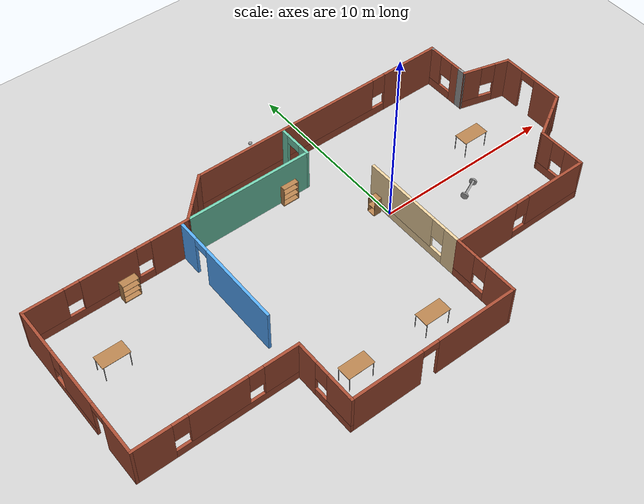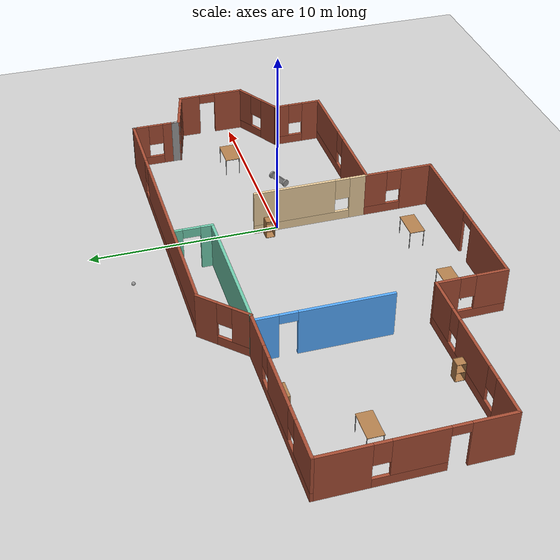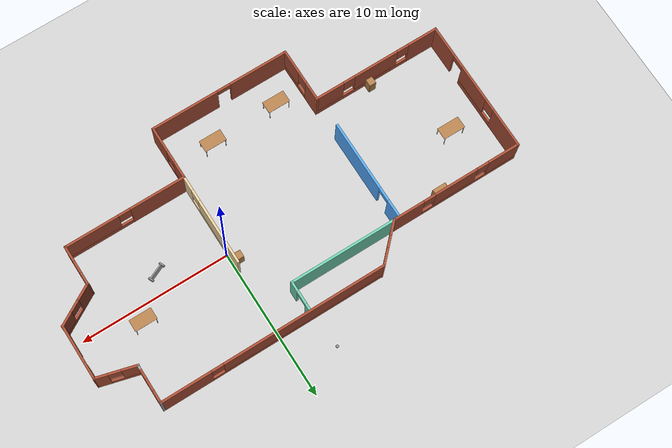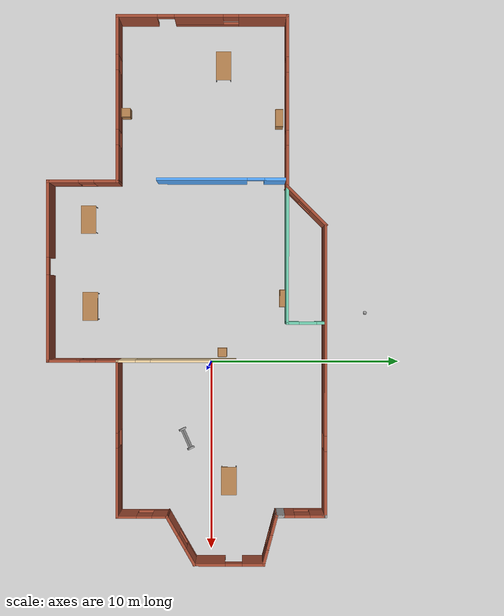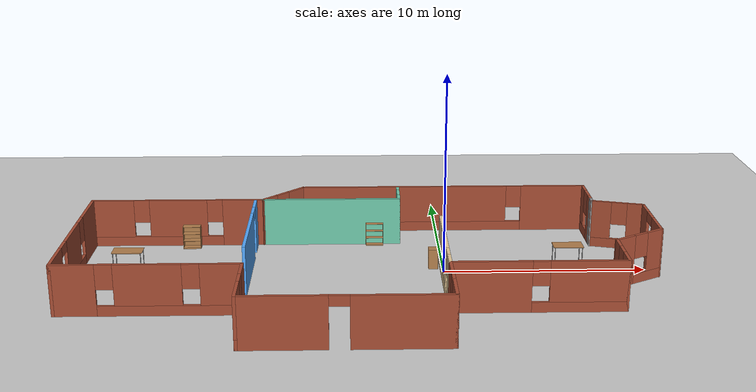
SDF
<sdf version="1.6">
 <world name="default">
  <plugin name="hello" filename="libhello.so"/>
  <light name="sun" type="directional">
   <pose>0 0 10 0 -0 0</pose>
   <diffuse>0.8 0.8 0.8 1</diffuse>
   <specular>0.2 0.2 0.2 1</specular>
   <attenuation>
    <range>1000</range>
    <constant>0.9</constant>
    <linear>0.01</linear>
    <quadratic>0.001</quadratic>
   </attenuation>
   <direction>-0.5 0.1 -0.9</direction>
  </light>
  <model name="ground_plane">
   <static>1</static>
   <link name="link">
    <collision name="collision">
     <geometry><plane><normal>0 0 1</normal><size>100 100</size></plane></geometry>
     <surface><friction><ode><mu>100</mu><mu2>50</mu2></ode></friction></surface>
    </collision>
    <visual name="visual">
     <cast_shadows>0</cast_shadows>
     <geometry><plane><normal>0 0 1</normal><size>100 100</size></plane></geometry>
     <material>
      <script><uri>file://media/materials/scripts/gazebo.material</uri><name>Gazebo/Grey</name></script>
     </material>
    </visual>
   </link>
  </model>
  <gravity>0 0 -9.8</gravity>
  <magnetic_field>6e-06 2.3e-05 -4.2e-05</magnetic_field>
  <atmosphere type="adiabatic"/>
  <physics name="default_physics" default="0" type="ode">
   <max_step_size>0.001</max_step_size>
   <real_time_factor>1</real_time_factor>
   <real_time_update_rate>1000</real_time_update_rate>
  </physics>
  <scene><ambient>0.4 0.4 0.4 1</ambient><background>0.7 0.7 0.7 1</background><shadows>1</shadows></scene>
  <spherical_coordinates>
   <surface_model>EARTH_WGS84</surface_model>
   <latitude_deg>0</latitude_deg>
   <longitude_deg>0</longitude_deg>
   <elevation>0</elevation>
   <heading_deg>0</heading_deg>
  </spherical_coordinates>
  <model name="robot">
   <link name="link_0">
    <inertial>
     <mass>1</mass>
     <inertia>
      <ixx>0.166667</ixx>
      <ixy>0</ixy>
      <ixz>0</ixz>
      <iyy>0.166667</iyy>
      <iyz>0</iyz>
      <izz>0.166667</izz>
     </inertia>
    </inertial>
    <visual name="visual">
     <geometry><box><size>0.3 1 0.1</size></box></geometry>
     <material>
      <lighting>1</lighting>
      <script><uri>file://media/materials/scripts/gazebo.material</uri><name>Gazebo/Grey</name></script>
      <ambient>0.3 0.3 0.3 1</ambient>
      <diffuse>0.7 0.7 0.7 1</diffuse>
      <specular>0.01 0.01 0.01 1</specular>
      <emissive>0 0 0 1</emissive>
      <shader type="vertex"><normal_map>__default__</normal_map></shader>
     </material>
    </visual>
    <collision name="collision">
     <geometry><box><size>0.3 1 0.1</size></box></geometry>
     <surface>
      <friction>
       <ode><mu>1</mu><mu2>1</mu2><fdir1>0 0 0</fdir1><slip1>0</slip1><slip2>0</slip2></ode>
       <torsional>
        <coefficient>1</coefficient>
        <patch_radius>0</patch_radius>
        <surface_radius>0</surface_radius>
        <use_patch_radius>1</use_patch_radius>
        <ode><slip>0</slip></ode>
       </torsional>
      </friction>
      <bounce><restitution_coefficient>0</restitution_coefficient><threshold>1e+06</threshold></bounce>
      <contact>
       <collide_without_contact>0</collide_without_contact>
       <collide_without_contact_bitmask>1</collide_without_contact_bitmask>
       <collide_bitmask>1</collide_bitmask>
       <ode>
        <soft_cfm>0</soft_cfm>
        <soft_erp>0.2</soft_erp>
        <kp>1e+13</kp>
        <kd>1</kd>
        <max_vel>0.01</max_vel>
        <min_depth>0</min_depth>
       </ode>
       <bullet>
        <split_impulse>1</split_impulse>
        <split_impulse_penetration_threshold>-0.01</split_impulse_penetration_threshold>
        <soft_cfm>0</soft_cfm>
        <soft_erp>0.2</soft_erp>
        <kp>1e+13</kp>
        <kd>1</kd>
       </bullet>
      </contact>
     </surface>
    </collision>
   </link>
   <link name="link_1">
    <pose>0 -0.550019 0 1.5707 -0 0</pose>
    <inertial>
     <mass>1</mass>
     <inertia><ixx>0.145833</ixx><ixy>0</ixy><ixz>0</ixz><iyy>0.145833</iyy><iyz>0</iyz><izz>0.125</izz></inertia>
    </inertial>
    <visual name="visual">
     <geometry><cylinder><radius>0.2</radius><length>0.1</length></cylinder></geometry>
     <material>
      <lighting>1</lighting>
      <script><uri>file://media/materials/scripts/gazebo.material</uri><name>Gazebo/Grey</name></script>
      <ambient>0.3 0.3 0.3 1</ambient>
      <diffuse>0.7 0.7 0.7 1</diffuse>
      <specular>0.01 0.01 0.01 1</specular>
      <emissive>0 0 0 1</emissive>
      <shader type="vertex"><normal_map>__default__</normal_map></shader>
     </material>
    </visual>
    <collision name="collision">
     <geometry><cylinder><radius>0.2</radius><length>0.1</length></cylinder></geometry>
     <surface>
      <friction>
       <ode><mu>1</mu><mu2>1</mu2><fdir1>0 0 0</fdir1><slip1>0</slip1><slip2>0</slip2></ode>
       <torsional>
        <coefficient>1</coefficient>
        <patch_radius>0</patch_radius>
        <surface_radius>0</surface_radius>
        <use_patch_radius>1</use_patch_radius>
        <ode><slip>0</slip></ode>
       </torsional>
      </friction>
      <bounce><restitution_coefficient>0</restitution_coefficient><threshold>1e+06</threshold></bounce>
      <contact>
       <collide_without_contact>0</collide_without_contact>
       <collide_without_contact_bitmask>1</collide_without_contact_bitmask>
       <collide_bitmask>1</collide_bitmask>
       <ode>
        <soft_cfm>0</soft_cfm>
        <soft_erp>0.2</soft_erp>
        <kp>1e+13</kp>
        <kd>1</kd>
        <max_vel>0.01</max_vel>
        <min_depth>0</min_depth>
       </ode>
       <bullet>
        <split_impulse>1</split_impulse>
        <split_impulse_penetration_threshold>-0.01</split_impulse_penetration_threshold>
        <soft_cfm>0</soft_cfm>
        <soft_erp>0.2</soft_erp>
        <kp>1e+13</kp>
        <kd>1</kd>
       </bullet>
      </contact>
     </surface>
    </collision>
   </link>
   <link name="link_1_clone">
    <pose>0 0.550019 0 1.5707 -0 0</pose>
    <inertial>
     <mass>1</mass>
     <inertia><ixx>0.145833</ixx><ixy>0</ixy><ixz>0</ixz><iyy>0.145833</iyy><iyz>0</iyz><izz>0.125</izz></inertia>
    </inertial>
    <visual name="visual">
     <geometry><cylinder><radius>0.2</radius><length>0.1</length></cylinder></geometry>
     <material>
      <lighting>1</lighting>
      <script><uri>file://media/materials/scripts/gazebo.material</uri><name>Gazebo/Grey</name></script>
      <ambient>0.3 0.3 0.3 1</ambient>
      <diffuse>0.7 0.7 0.7 1</diffuse>
      <specular>0.01 0.01 0.01 1</specular>
      <emissive>0 0 0 1</emissive>
      <shader type="vertex"><normal_map>__default__</normal_map></shader>
     </material>
    </visual>
    <collision name="collision">
     <geometry><cylinder><radius>0.2</radius><length>0.1</length></cylinder></geometry>
     <surface>
      <friction>
       <ode><mu>1</mu><mu2>1</mu2><fdir1>0 0 0</fdir1><slip1>0</slip1><slip2>0</slip2></ode>
       <torsional>
        <coefficient>1</coefficient>
        <patch_radius>0</patch_radius>
        <surface_radius>0</surface_radius>
        <use_patch_radius>1</use_patch_radius>
        <ode><slip>0</slip></ode>
       </torsional>
      </friction>
      <bounce><restitution_coefficient>0</restitution_coefficient><threshold>1e+06</threshold></bounce>
      <contact>
       <collide_without_contact>0</collide_without_contact>
       <collide_without_contact_bitmask>1</collide_without_contact_bitmask>
       <collide_bitmask>1</collide_bitmask>
       <ode>
        <soft_cfm>0</soft_cfm>
        <soft_erp>0.2</soft_erp>
        <kp>1e+13</kp>
        <kd>1</kd>
        <max_vel>0.01</max_vel>
        <min_depth>0</min_depth>
       </ode>
       <bullet>
        <split_impulse>1</split_impulse>
        <split_impulse_penetration_threshold>-0.01</split_impulse_penetration_threshold>
        <soft_cfm>0</soft_cfm>
        <soft_erp>0.2</soft_erp>
        <kp>1e+13</kp>
        <kd>1</kd>
       </bullet>
      </contact>
     </surface>
    </collision>
   </link>
   <joint name="link_0_JOINT_0" type="revolute">
    <parent>link_0</parent>
    <child>link_1</child>
    <axis>
     <xyz>0 0 1</xyz>
     <use_parent_model_frame>0</use_parent_model_frame>
     <limit>
      <lower>-1.79769e+308</lower>
      <upper>1.79769e+308</upper>
      <effort>-1</effort>
      <velocity>-1</velocity>
     </limit>
     <dynamics>
      <spring_reference>0</spring_reference>
      <spring_stiffness>0</spring_stiffness>
      <damping>0</damping>
     </dynamics>
    </axis>
    <physics>
     <ode><limit><cfm>0</cfm><erp>0.2</erp></limit><suspension><cfm>0</cfm><erp>0.2</erp></suspension></ode>
    </physics>
   </joint>
   <joint name="link_0_JOINT_1" type="revolute">
    <parent>link_0</parent>
    <child>link_1_clone</child>
    <axis>
     <xyz>0 0 1</xyz>
     <use_parent_model_frame>0</use_parent_model_frame>
     <limit>
      <lower>-1.79769e+308</lower>
      <upper>1.79769e+308</upper>
      <effort>-1</effort>
      <velocity>-1</velocity>
     </limit>
     <dynamics>
      <spring_reference>0</spring_reference>
      <spring_stiffness>0</spring_stiffness>
      <damping>0</damping>
     </dynamics>
    </axis>
    <physics>
     <ode><limit><cfm>0</cfm><erp>0.2</erp></limit><suspension><cfm>0</cfm><erp>0.2</erp></suspension></ode>
    </physics>
   </joint>
   <static>0</static>
   <pose>4.12273 -1.3212 0.200002 3.14159 1.21121 1.98891</pose>
  </model>
  <model name="brickhouse">
   <pose>-3.77713 -1.2088 0 0 -0 0</pose>
   <link name="Wall_1">
    <pose>-4.41518 6.20947 0 0 0 -2.35619</pose>
    <visual name="Wall_1_Visual_0">
     <pose>-0.913281 0 1.25 0 -0 0</pose>
     <geometry><box><size>1.17344 0.15 2.5</size></box></geometry>
     <material>
      <script><uri>file://media/materials/scripts/gazebo.material</uri><name>Gazebo/Bricks</name></script>
      <ambient>1 1 1 1</ambient>
     </material>
     <meta><layer>0</layer></meta>
    </visual>
    <collision name="Wall_1_Collision_0">
     <geometry><box><size>1.17344 0.15 2.5</size></box></geometry>
     <pose>-0.913281 0 1.25 0 -0 0</pose>
    </collision>
    <visual name="Wall_1_Visual_1">
     <pose>0.586719 0 0.25 0 -0 0</pose>
     <geometry><box><size>1.82656 0.15 0.5</size></box></geometry>
     <material>
      <script><uri>file://media/materials/scripts/gazebo.material</uri><name>Gazebo/Bricks</name></script>
      <ambient>1 1 1 1</ambient>
     </material>
     <meta><layer>0</layer></meta>
    </visual>
    <collision name="Wall_1_Collision_1">
     <geometry><box><size>1.82656 0.15 0.5</size></box></geometry>
     <pose>0.586719 0 0.25 0 -0 0</pose>
    </collision>
    <visual name="Wall_1_Visual_2">
     <pose>0.986719 0 1.5 0 -0 0</pose>
     <geometry><box><size>1.02656 0.15 2</size></box></geometry>
     <material>
      <script><uri>file://media/materials/scripts/gazebo.material</uri><name>Gazebo/Bricks</name></script>
      <ambient>1 1 1 1</ambient>
     </material>
     <meta><layer>0</layer></meta>
    </visual>
    <collision name="Wall_1_Collision_2">
     <geometry><box><size>1.02656 0.15 2</size></box></geometry>
     <pose>0.986719 0 1.5 0 -0 0</pose>
    </collision>
    <visual name="Wall_1_Visual_3">
     <pose>0.073438 0 1.9 0 -0 0</pose>
     <geometry><box><size>0.8 0.15 1.2</size></box></geometry>
     <material>
      <script><uri>file://media/materials/scripts/gazebo.material</uri><name>Gazebo/Bricks</name></script>
      <ambient>1 1 1 1</ambient>
     </material>
     <meta><layer>0</layer></meta>
    </visual>
    <collision name="Wall_1_Collision_3">
     <geometry><box><size>0.8 0.15 1.2</size></box></geometry>
     <pose>0.073438 0 1.9 0 -0 0</pose>
    </collision>
   </link>
   <link name="Wall_10">
    <pose>13.0113 -0.33566 0 0 -0 0.523599</pose>
    <visual name="Wall_10_Visual_0">
     <pose>-0.906095 0 1.25 0 -0 0</pose>
     <geometry><box><size>1.18781 0.15 2.5</size></box></geometry>
     <material>
      <script><uri>file://media/materials/scripts/gazebo.material</uri><name>Gazebo/Bricks</name></script>
      <ambient>1 1 1 1</ambient>
     </material>
     <meta><layer>0</layer></meta>
    </visual>
    <collision name="Wall_10_Collision_0">
     <geometry><box><size>1.18781 0.15 2.5</size></box></geometry>
     <pose>-0.906095 0 1.25 0 -0 0</pose>
    </collision>
    <visual name="Wall_10_Visual_1">
     <pose>0.593905 0 0.25 0 -0 0</pose>
     <geometry><box><size>1.81219 0.15 0.5</size></box></geometry>
     <material>
      <script><uri>file://media/materials/scripts/gazebo.material</uri><name>Gazebo/Bricks</name></script>
      <ambient>1 1 1 1</ambient>
     </material>
     <meta><layer>0</layer></meta>
    </visual>
    <collision name="Wall_10_Collision_1">
     <geometry><box><size>1.81219 0.15 0.5</size></box></geometry>
     <pose>0.593905 0 0.25 0 -0 0</pose>
    </collision>
    <visual name="Wall_10_Visual_2">
     <pose>0.993905 0 1.5 0 -0 0</pose>
     <geometry><box><size>1.01219 0.15 2</size></box></geometry>
     <material>
      <script><uri>file://media/materials/scripts/gazebo.material</uri><name>Gazebo/Bricks</name></script>
      <ambient>1 1 1 1</ambient>
     </material>
     <meta><layer>0</layer></meta>
    </visual>
    <collision name="Wall_10_Collision_2">
     <geometry><box><size>1.01219 0.15 2</size></box></geometry>
     <pose>0.993905 0 1.5 0 -0 0</pose>
    </collision>
    <visual name="Wall_10_Visual_3">
     <pose>0.087809 0 1.9 0 -0 0</pose>
     <geometry><box><size>0.8 0.15 1.2</size></box></geometry>
     <material>
      <script><uri>file://media/materials/scripts/gazebo.material</uri><name>Gazebo/Bricks</name></script>
      <ambient>1 1 1 1</ambient>
     </material>
     <meta><layer>0</layer></meta>
    </visual>
    <collision name="Wall_10_Collision_3">
     <geometry><box><size>0.8 0.15 1.2</size></box></geometry>
     <pose>0.087809 0 1.9 0 -0 0</pose>
    </collision>
   </link>
   <link name="Wall_11">
    <pose>14.2454 2.17684 0 0 -0 1.5708</pose>
    <visual name="Wall_11_Visual_0">
     <pose>-1.04258 0 1.25 0 -0 0</pose>
     <geometry><box><size>1.66484 0.15 2.5</size></box></geometry>
     <material>
      <script><uri>file://media/materials/scripts/gazebo.material</uri><name>Gazebo/Bricks</name></script>
      <ambient>1 1 1 1</ambient>
     </material>
     <meta><layer>0</layer></meta>
    </visual>
    <collision name="Wall_11_Collision_0">
     <geometry><box><size>1.66484 0.15 2.5</size></box></geometry>
     <pose>-1.04258 0 1.25 0 -0 0</pose>
    </collision>
    <visual name="Wall_11_Visual_1">
     <pose>1.28242 0 1.25 0 -0 0</pose>
     <geometry><box><size>1.18516 0.15 2.5</size></box></geometry>
     <material>
      <script><uri>file://media/materials/scripts/gazebo.material</uri><name>Gazebo/Bricks</name></script>
      <ambient>1 1 1 1</ambient>
     </material>
     <meta><layer>0</layer></meta>
    </visual>
    <collision name="Wall_11_Collision_1">
     <geometry><box><size>1.18516 0.15 2.5</size></box></geometry>
     <pose>1.28242 0 1.25 0 -0 0</pose>
    </collision>
    <visual name="Wall_11_Visual_2">
     <pose>0.239836 0 2.25 0 -0 0</pose>
     <geometry><box><size>0.9 0.15 0.5</size></box></geometry>
     <material>
      <script><uri>file://media/materials/scripts/gazebo.material</uri><name>Gazebo/Bricks</name></script>
      <ambient>1 1 1 1</ambient>
     </material>
     <meta><layer>0</layer></meta>
    </visual>
    <collision name="Wall_11_Collision_2">
     <geometry><box><size>0.9 0.15 0.5</size></box></geometry>
     <pose>0.239836 0 2.25 0 -0 0</pose>
    </collision>
   </link>
   <link name="Wall_12">
    <pose>12.9897 4.3133 0 0 -0 2.87979</pose>
    <visual name="Wall_12_Visual_0">
     <pose>-0.936482 0 1.25 0 -0 0</pose>
     <geometry><box><size>0.877036 0.15 2.5</size></box></geometry>
     <material>
      <script><uri>file://media/materials/scripts/gazebo.material</uri><name>Gazebo/Bricks</name></script>
      <ambient>1 1 1 1</ambient>
     </material>
     <meta><layer>0</layer></meta>
    </visual>
    <collision name="Wall_12_Collision_0">
     <geometry><box><size>0.877036 0.15 2.5</size></box></geometry>
     <pose>-0.936482 0 1.25 0 -0 0</pose>
    </collision>
    <visual name="Wall_12_Visual_1">
     <pose>0.438518 0 0.25 0 -0 0</pose>
     <geometry><box><size>1.87296 0.15 0.5</size></box></geometry>
     <material>
      <script><uri>file://media/materials/scripts/gazebo.material</uri><name>Gazebo/Bricks</name></script>
      <ambient>1 1 1 1</ambient>
     </material>
     <meta><layer>0</layer></meta>
    </visual>
    <collision name="Wall_12_Collision_1">
     <geometry><box><size>1.87296 0.15 0.5</size></box></geometry>
     <pose>0.438518 0 0.25 0 -0 0</pose>
    </collision>
    <visual name="Wall_12_Visual_2">
     <pose>0.838518 0 1.5 0 -0 0</pose>
     <geometry><box><size>1.07296 0.15 2</size></box></geometry>
     <material>
      <script><uri>file://media/materials/scripts/gazebo.material</uri><name>Gazebo/Bricks</name></script>
      <ambient>1 1 1 1</ambient>
     </material>
     <meta><layer>0</layer></meta>
    </visual>
    <collision name="Wall_12_Collision_2">
     <geometry><box><size>1.07296 0.15 2</size></box></geometry>
     <pose>0.838518 0 1.5 0 -0 0</pose>
    </collision>
    <visual name="Wall_12_Visual_3">
     <pose>-0.097964 0 1.9 0 -0 0</pose>
     <geometry><box><size>0.8 0.15 1.2</size></box></geometry>
     <material>
      <script><uri>file://media/materials/scripts/gazebo.material</uri><name>Gazebo/Bricks</name></script>
      <ambient>1 1 1 1</ambient>
     </material>
     <meta><layer>0</layer></meta>
    </visual>
    <collision name="Wall_12_Collision_3">
     <geometry><box><size>0.8 0.15 1.2</size></box></geometry>
     <pose>-0.097964 0 1.9 0 -0 0</pose>
    </collision>
   </link>
   <link name="Wall_13">
    <collision name="Wall_13_Collision">
     <geometry><box><size>0.5 0.15 2.5</size></box></geometry>
     <pose>0 0 1.25 0 -0 0</pose>
    </collision>
    <visual name="Wall_13_Visual">
     <pose>0 0 1.25 0 -0 0</pose>
     <geometry><box><size>0.5 0.15 2.5</size></box></geometry>
     <material>
      <script><uri>file://media/materials/scripts/gazebo.material</uri><name>Gazebo/Grey</name></script>
      <ambient>1 1 1 1</ambient>
     </material>
     <meta><layer>0</layer></meta>
    </visual>
    <pose>11.734 4.82477 0 0 -0 1.5708</pose>
   </link>
   <link name="Wall_14">
    <pose>11.734 6.04977 0 0 -0 1.5708</pose>
    <visual name="Wall_14_Visual_0">
     <pose>-0.797565 0 1.25 0 -0 0</pose>
     <geometry><box><size>0.65487 0.15 2.5</size></box></geometry>
     <material>
      <script><uri>file://media/materials/scripts/gazebo.material</uri><name>Gazebo/Bricks</name></script>
      <ambient>1 1 1 1</ambient>
     </material>
     <meta><layer>0</layer></meta>
    </visual>
    <collision name="Wall_14_Collision_0">
     <geometry><box><size>0.65487 0.15 2.5</size></box></geometry>
     <pose>-0.797565 0 1.25 0 -0 0</pose>
    </collision>
    <visual name="Wall_14_Visual_1">
     <pose>0.327435 0 0.25 0 -0 0</pose>
     <geometry><box><size>1.59513 0.15 0.5</size></box></geometry>
     <material>
      <script><uri>file://media/materials/scripts/gazebo.material</uri><name>Gazebo/Bricks</name></script>
      <ambient>1 1 1 1</ambient>
     </material>
     <meta><layer>0</layer></meta>
    </visual>
    <collision name="Wall_14_Collision_1">
     <geometry><box><size>1.59513 0.15 0.5</size></box></geometry>
     <pose>0.327435 0 0.25 0 -0 0</pose>
    </collision>
    <visual name="Wall_14_Visual_2">
     <pose>0.727435 0 1.5 0 -0 0</pose>
     <geometry><box><size>0.79513 0.15 2</size></box></geometry>
     <material>
      <script><uri>file://media/materials/scripts/gazebo.material</uri><name>Gazebo/Bricks</name></script>
      <ambient>1 1 1 1</ambient>
     </material>
     <meta><layer>0</layer></meta>
    </visual>
    <collision name="Wall_14_Collision_2">
     <geometry><box><size>0.79513 0.15 2</size></box></geometry>
     <pose>0.727435 0 1.5 0 -0 0</pose>
    </collision>
    <visual name="Wall_14_Visual_3">
     <pose>-0.07013 0 1.9 0 -0 0</pose>
     <geometry><box><size>0.8 0.15 1.2</size></box></geometry>
     <material>
      <script><uri>file://media/materials/scripts/gazebo.material</uri><name>Gazebo/Bricks</name></script>
      <ambient>1 1 1 1</ambient>
     </material>
     <meta><layer>0</layer></meta>
    </visual>
    <collision name="Wall_14_Collision_3">
     <geometry><box><size>0.8 0.15 1.2</size></box></geometry>
     <pose>-0.07013 0 1.9 0 -0 0</pose>
    </collision>
   </link>
   <link name="Wall_15">
    <collision name="Wall_15_Collision">
     <geometry><box><size>0.25 0.15 2.5</size></box></geometry>
     <pose>0 0 1.25 0 -0 0</pose>
    </collision>
    <visual name="Wall_15_Visual">
     <pose>0 0 1.25 0 -0 0</pose>
     <geometry><box><size>0.25 0.15 2.5</size></box></geometry>
     <material>
      <script><uri>file://media/materials/scripts/gazebo.material</uri><name>Gazebo/Grey</name></script>
      <ambient>1 1 1 1</ambient>
     </material>
     <meta><layer>0</layer></meta>
    </visual>
    <pose>11.734 7.14977 0 0 -0 1.5708</pose>
   </link>
   <link name="Wall_16">
    <pose>4.18395 7.19977 0 0 -0 3.14159</pose>
    <visual name="Wall_16_Visual_0">
     <pose>-5.89816 0 1.25 0 -0 0</pose>
     <geometry><box><size>3.45369 0.15 2.5</size></box></geometry>
     <material>
      <script><uri>file://media/materials/scripts/gazebo.material</uri><name>Gazebo/Bricks</name></script>
      <ambient>1 1 1 1</ambient>
     </material>
     <meta><layer>0</layer></meta>
    </visual>
    <collision name="Wall_16_Collision_0">
     <geometry><box><size>3.45369 0.15 2.5</size></box></geometry>
     <pose>-5.89816 0 1.25 0 -0 0</pose>
    </collision>
    <visual name="Wall_16_Visual_1">
     <pose>1.72684 0 0.25 0 -0 0</pose>
     <geometry><box><size>11.7963 0.15 0.5</size></box></geometry>
     <material>
      <script><uri>file://media/materials/scripts/gazebo.material</uri><name>Gazebo/Bricks</name></script>
      <ambient>1 1 1 1</ambient>
     </material>
     <meta><layer>0</layer></meta>
    </visual>
    <collision name="Wall_16_Collision_1">
     <geometry><box><size>11.7963 0.15 0.5</size></box></geometry>
     <pose>1.72684 0 0.25 0 -0 0</pose>
    </collision>
    <visual name="Wall_16_Visual_2">
     <pose>2.12684 0 1.5 0 -0 0</pose>
     <geometry><box><size>10.9963 0.15 2</size></box></geometry>
     <material>
      <script><uri>file://media/materials/scripts/gazebo.material</uri><name>Gazebo/Bricks</name></script>
      <ambient>1 1 1 1</ambient>
     </material>
     <meta><layer>0</layer></meta>
    </visual>
    <collision name="Wall_16_Collision_2">
     <geometry><box><size>10.9963 0.15 2</size></box></geometry>
     <pose>2.12684 0 1.5 0 -0 0</pose>
    </collision>
    <visual name="Wall_16_Visual_3">
     <pose>-3.77131 0 1.9 0 -0 0</pose>
     <geometry><box><size>0.8 0.15 1.2</size></box></geometry>
     <material>
      <script><uri>file://media/materials/scripts/gazebo.material</uri><name>Gazebo/Bricks</name></script>
      <ambient>1 1 1 1</ambient>
     </material>
     <meta><layer>0</layer></meta>
    </visual>
    <collision name="Wall_16_Collision_3">
     <geometry><box><size>0.8 0.15 1.2</size></box></geometry>
     <pose>-3.77131 0 1.9 0 -0 0</pose>
    </collision>
   </link>
   <link name="Wall_18">
    <pose>-5.79963 1.75078 0 0 -0 1.5708</pose>
    <visual name="Wall_18_Visual_0">
     <pose>-1.01174 0 1.25 0 -0 0</pose>
     <geometry><box><size>4.72653 0.15 2.5</size></box></geometry>
     <material>
      <script><uri>file://media/materials/scripts/gazebo.material</uri><name>Gazebo/Grey</name></script>
      <ambient>0.333333 0.666667 1 1</ambient>
     </material>
     <meta><layer>0</layer></meta>
    </visual>
    <collision name="Wall_18_Collision_0">
     <geometry><box><size>4.72653 0.15 2.5</size></box></geometry>
     <pose>-1.01174 0 1.25 0 -0 0</pose>
    </collision>
    <visual name="Wall_18_Visual_1">
     <pose>2.81326 0 1.25 0 -0 0</pose>
     <geometry><box><size>1.12347 0.15 2.5</size></box></geometry>
     <material>
      <script><uri>file://media/materials/scripts/gazebo.material</uri><name>Gazebo/Grey</name></script>
      <ambient>0.333333 0.666667 1 1</ambient>
     </material>
     <meta><layer>0</layer></meta>
    </visual>
    <collision name="Wall_18_Collision_1">
     <geometry><box><size>1.12347 0.15 2.5</size></box></geometry>
     <pose>2.81326 0 1.25 0 -0 0</pose>
    </collision>
    <visual name="Wall_18_Visual_2">
     <pose>1.80153 0 2.25 0 -0 0</pose>
     <geometry><box><size>0.9 0.15 0.5</size></box></geometry>
     <material>
      <script><uri>file://media/materials/scripts/gazebo.material</uri><name>Gazebo/Grey</name></script>
      <ambient>0.333333 0.666667 1 1</ambient>
     </material>
     <meta><layer>0</layer></meta>
    </visual>
    <collision name="Wall_18_Collision_2">
     <geometry><box><size>0.9 0.15 0.5</size></box></geometry>
     <pose>1.80153 0 2.25 0 -0 0</pose>
    </collision>
   </link>
   <link name="Wall_2">
    <pose>-9.84781 5.20184 0 0 -0 3.14159</pose>
    <visual name="Wall_2_Visual_0">
     <pose>-3.40202 0 1.25 0 -0 0</pose>
     <geometry><box><size>2.19596 0.15 2.5</size></box></geometry>
     <material>
      <script><uri>file://media/materials/scripts/gazebo.material</uri><name>Gazebo/Bricks</name></script>
      <ambient>1 1 1 1</ambient>
     </material>
     <meta><layer>0</layer></meta>
    </visual>
    <collision name="Wall_2_Collision_0">
     <geometry><box><size>2.19596 0.15 2.5</size></box></geometry>
     <pose>-3.40202 0 1.25 0 -0 0</pose>
    </collision>
    <visual name="Wall_2_Visual_1">
     <pose>1.09798 0 0.25 0 -0 0</pose>
     <geometry><box><size>6.80404 0.15 0.5</size></box></geometry>
     <material>
      <script><uri>file://media/materials/scripts/gazebo.material</uri><name>Gazebo/Bricks</name></script>
      <ambient>1 1 1 1</ambient>
     </material>
     <meta><layer>0</layer></meta>
    </visual>
    <collision name="Wall_2_Collision_1">
     <geometry><box><size>6.80404 0.15 0.5</size></box></geometry>
     <pose>1.09798 0 0.25 0 -0 0</pose>
    </collision>
    <visual name="Wall_2_Visual_2">
     <pose>-0.002627 0 1.5 0 -0 0</pose>
     <geometry><box><size>3.00283 0.15 2</size></box></geometry>
     <material>
      <script><uri>file://media/materials/scripts/gazebo.material</uri><name>Gazebo/Bricks</name></script>
      <ambient>1 1 1 1</ambient>
     </material>
     <meta><layer>0</layer></meta>
    </visual>
    <collision name="Wall_2_Collision_2">
     <geometry><box><size>3.00283 0.15 2</size></box></geometry>
     <pose>-0.002627 0 1.5 0 -0 0</pose>
    </collision>
    <visual name="Wall_2_Visual_3">
     <pose>3.39939 0 1.5 0 -0 0</pose>
     <geometry><box><size>2.20121 0.15 2</size></box></geometry>
     <material>
      <script><uri>file://media/materials/scripts/gazebo.material</uri><name>Gazebo/Bricks</name></script>
      <ambient>1 1 1 1</ambient>
     </material>
     <meta><layer>0</layer></meta>
    </visual>
    <collision name="Wall_2_Collision_3">
     <geometry><box><size>2.20121 0.15 2</size></box></geometry>
     <pose>3.39939 0 1.5 0 -0 0</pose>
    </collision>
    <visual name="Wall_2_Visual_4">
     <pose>-1.90404 0 1.9 0 -0 0</pose>
     <geometry><box><size>0.8 0.15 1.2</size></box></geometry>
     <material>
      <script><uri>file://media/materials/scripts/gazebo.material</uri><name>Gazebo/Bricks</name></script>
      <ambient>1 1 1 1</ambient>
     </material>
     <meta><layer>0</layer></meta>
    </visual>
    <collision name="Wall_2_Collision_4">
     <geometry><box><size>0.8 0.15 1.2</size></box></geometry>
     <pose>-1.90404 0 1.9 0 -0 0</pose>
    </collision>
    <visual name="Wall_2_Visual_5">
     <pose>1.89879 0 1.9 0 -0 0</pose>
     <geometry><box><size>0.8 0.15 1.2</size></box></geometry>
     <material>
      <script><uri>file://media/materials/scripts/gazebo.material</uri><name>Gazebo/Bricks</name></script>
      <ambient>1 1 1 1</ambient>
     </material>
     <meta><layer>0</layer></meta>
    </visual>
    <collision name="Wall_2_Collision_5">
     <geometry><box><size>0.8 0.15 1.2</size></box></geometry>
     <pose>1.89879 0 1.9 0 -0 0</pose>
    </collision>
   </link>
   <link name="Wall_21">
    <collision name="Wall_21_Collision">
     <geometry><box><size>7.25 0.15 2.5</size></box></geometry>
     <pose>0 0 1.25 0 -0 0</pose>
    </collision>
    <visual name="Wall_21_Visual">
     <pose>0 0 1.25 0 -0 0</pose>
     <geometry><box><size>7.25 0.15 2.5</size></box></geometry>
     <material>
      <script><uri>file://media/materials/scripts/gazebo.material</uri><name>Gazebo/Grey</name></script>
      <ambient>0.435294 0.796078 0.67451 1</ambient>
     </material>
     <meta><layer>0</layer></meta>
    </visual>
    <pose>-1.87281 5.20184 0 0 -0 0</pose>
   </link>
   <link name="Wall_22">
    <pose>1.67719 6.12684 0 0 -0 1.5708</pose>
    <visual name="Wall_22_Visual_0">
     <pose>-0.657006 0 1.25 0 -0 0</pose>
     <geometry><box><size>0.685988 0.15 2.5</size></box></geometry>
     <material>
      <script><uri>file://media/materials/scripts/gazebo.material</uri><name>Gazebo/Grey</name></script>
      <ambient>0.435294 0.796078 0.67451 1</ambient>
     </material>
     <meta><layer>0</layer></meta>
    </visual>
    <collision name="Wall_22_Collision_0">
     <geometry><box><size>0.685988 0.15 2.5</size></box></geometry>
     <pose>-0.657006 0 1.25 0 -0 0</pose>
    </collision>
    <visual name="Wall_22_Visual_1">
     <pose>0.792994 0 1.25 0 -0 0</pose>
     <geometry><box><size>0.414012 0.15 2.5</size></box></geometry>
     <material>
      <script><uri>file://media/materials/scripts/gazebo.material</uri><name>Gazebo/Grey</name></script>
      <ambient>0.435294 0.796078 0.67451 1</ambient>
     </material>
     <meta><layer>0</layer></meta>
    </visual>
    <collision name="Wall_22_Collision_1">
     <geometry><box><size>0.414012 0.15 2.5</size></box></geometry>
     <pose>0.792994 0 1.25 0 -0 0</pose>
    </collision>
    <visual name="Wall_22_Visual_2">
     <pose>0.135988 0 2.25 0 -0 0</pose>
     <geometry><box><size>0.9 0.15 0.5</size></box></geometry>
     <material>
      <script><uri>file://media/materials/scripts/gazebo.material</uri><name>Gazebo/Grey</name></script>
      <ambient>0.435294 0.796078 0.67451 1</ambient>
     </material>
     <meta><layer>0</layer></meta>
    </visual>
    <collision name="Wall_22_Collision_2">
     <geometry><box><size>0.9 0.15 0.5</size></box></geometry>
     <pose>0.135988 0 2.25 0 -0 0</pose>
    </collision>
   </link>
   <link name="Wall_26">
    <pose>3.67719 -0.59816 0 0 -0 1.5708</pose>
    <visual name="Wall_26_Visual_0">
     <pose>-2.6203 0 1.25 0 -0 0</pose>
     <geometry><box><size>1.00941 0.15 2.5</size></box></geometry>
     <material>
      <script><uri>file://media/materials/scripts/gazebo.material</uri><name>Gazebo/Grey</name></script>
      <ambient>0.921569 0.807843 0.615686 1</ambient>
     </material>
     <meta><layer>0</layer></meta>
    </visual>
    <collision name="Wall_26_Collision_0">
     <geometry><box><size>1.00941 0.15 2.5</size></box></geometry>
     <pose>-2.6203 0 1.25 0 -0 0</pose>
    </collision>
    <visual name="Wall_26_Visual_1">
     <pose>0.504703 0 0.25 0 -0 0</pose>
     <geometry><box><size>5.24059 0.15 0.5</size></box></geometry>
     <material>
      <script><uri>file://media/materials/scripts/gazebo.material</uri><name>Gazebo/Grey</name></script>
      <ambient>0.921569 0.807843 0.615686 1</ambient>
     </material>
     <meta><layer>0</layer></meta>
    </visual>
    <collision name="Wall_26_Collision_1">
     <geometry><box><size>5.24059 0.15 0.5</size></box></geometry>
     <pose>0.504703 0 0.25 0 -0 0</pose>
    </collision>
    <visual name="Wall_26_Visual_2">
     <pose>0.904703 0 1.5 0 -0 0</pose>
     <geometry><box><size>4.44059 0.15 2</size></box></geometry>
     <material>
      <script><uri>file://media/materials/scripts/gazebo.material</uri><name>Gazebo/Grey</name></script>
      <ambient>0.921569 0.807843 0.615686 1</ambient>
     </material>
     <meta><layer>0</layer></meta>
    </visual>
    <collision name="Wall_26_Collision_2">
     <geometry><box><size>4.44059 0.15 2</size></box></geometry>
     <pose>0.904703 0 1.5 0 -0 0</pose>
    </collision>
    <visual name="Wall_26_Visual_3">
     <pose>-1.71559 0 1.9 0 -0 0</pose>
     <geometry><box><size>0.8 0.15 1.2</size></box></geometry>
     <material>
      <script><uri>file://media/materials/scripts/gazebo.material</uri><name>Gazebo/Grey</name></script>
      <ambient>0.921569 0.807843 0.615686 1</ambient>
     </material>
     <meta><layer>0</layer></meta>
    </visual>
    <collision name="Wall_26_Collision_3">
     <geometry><box><size>0.8 0.15 1.2</size></box></geometry>
     <pose>-1.71559 0 1.9 0 -0 0</pose>
    </collision>
   </link>
   <link name="Wall_3">
    <pose>-14.2728 0.77684 0 0 0 -1.5708</pose>
    <visual name="Wall_3_Visual_0">
     <pose>-3.19044 0 1.25 0 -0 0</pose>
     <geometry><box><size>2.61911 0.15 2.5</size></box></geometry>
     <material>
      <script><uri>file://media/materials/scripts/gazebo.material</uri><name>Gazebo/Bricks</name></script>
      <ambient>1 1 1 1</ambient>
     </material>
     <meta><layer>0</layer></meta>
    </visual>
    <collision name="Wall_3_Collision_0">
     <geometry><box><size>2.61911 0.15 2.5</size></box></geometry>
     <pose>-3.19044 0 1.25 0 -0 0</pose>
    </collision>
    <visual name="Wall_3_Visual_1">
     <pose>3.42825 0 1.25 0 -0 0</pose>
     <geometry><box><size>2.14351 0.15 2.5</size></box></geometry>
     <material>
      <script><uri>file://media/materials/scripts/gazebo.material</uri><name>Gazebo/Bricks</name></script>
      <ambient>1 1 1 1</ambient>
     </material>
     <meta><layer>0</layer></meta>
    </visual>
    <collision name="Wall_3_Collision_1">
     <geometry><box><size>2.14351 0.15 2.5</size></box></geometry>
     <pose>3.42825 0 1.25 0 -0 0</pose>
    </collision>
    <visual name="Wall_3_Visual_2">
     <pose>-0.212197 0 0.25 0 -0 0</pose>
     <geometry><box><size>3.33738 0.15 0.5</size></box></geometry>
     <material>
      <script><uri>file://media/materials/scripts/gazebo.material</uri><name>Gazebo/Bricks</name></script>
      <ambient>1 1 1 1</ambient>
     </material>
     <meta><layer>0</layer></meta>
    </visual>
    <collision name="Wall_3_Collision_2">
     <geometry><box><size>3.33738 0.15 0.5</size></box></geometry>
     <pose>-0.212197 0 0.25 0 -0 0</pose>
    </collision>
    <visual name="Wall_3_Visual_3">
     <pose>0.187803 0 1.5 0 -0 0</pose>
     <geometry><box><size>2.53738 0.15 2</size></box></geometry>
     <material>
      <script><uri>file://media/materials/scripts/gazebo.material</uri><name>Gazebo/Bricks</name></script>
      <ambient>1 1 1 1</ambient>
     </material>
     <meta><layer>0</layer></meta>
    </visual>
    <collision name="Wall_3_Collision_3">
     <geometry><box><size>2.53738 0.15 2</size></box></geometry>
     <pose>0.187803 0 1.5 0 -0 0</pose>
    </collision>
    <visual name="Wall_3_Visual_4">
     <pose>-1.48089 0 1.9 0 -0 0</pose>
     <geometry><box><size>0.8 0.15 1.2</size></box></geometry>
     <material>
      <script><uri>file://media/materials/scripts/gazebo.material</uri><name>Gazebo/Bricks</name></script>
      <ambient>1 1 1 1</ambient>
     </material>
     <meta><layer>0</layer></meta>
    </visual>
    <collision name="Wall_3_Collision_4">
     <geometry><box><size>0.8 0.15 1.2</size></box></geometry>
     <pose>-1.48089 0 1.9 0 -0 0</pose>
    </collision>
    <visual name="Wall_3_Visual_5">
     <pose>1.90649 0 2.25 0 -0 0</pose>
     <geometry><box><size>0.9 0.15 0.5</size></box></geometry>
     <material>
      <script><uri>file://media/materials/scripts/gazebo.material</uri><name>Gazebo/Bricks</name></script>
      <ambient>1 1 1 1</ambient>
     </material>
     <meta><layer>0</layer></meta>
    </visual>
    <collision name="Wall_3_Collision_5">
     <geometry><box><size>0.9 0.15 0.5</size></box></geometry>
     <pose>1.90649 0 2.25 0 -0 0</pose>
    </collision>
   </link>
   <link name="Wall_4">
    <pose>-9.97281 -3.64816 0 0 -0 0</pose>
    <visual name="Wall_4_Visual_0">
     <pose>-3.33508 0 1.25 0 -0 0</pose>
     <geometry><box><size>2.07985 0.15 2.5</size></box></geometry>
     <material>
      <script><uri>file://media/materials/scripts/gazebo.material</uri><name>Gazebo/Bricks</name></script>
      <ambient>1 1 1 1</ambient>
     </material>
     <meta><layer>0</layer></meta>
    </visual>
    <collision name="Wall_4_Collision_0">
     <geometry><box><size>2.07985 0.15 2.5</size></box></geometry>
     <pose>-3.33508 0 1.25 0 -0 0</pose>
    </collision>
    <visual name="Wall_4_Visual_1">
     <pose>1.03992 0 0.25 0 -0 0</pose>
     <geometry><box><size>6.67015 0.15 0.5</size></box></geometry>
     <material>
      <script><uri>file://media/materials/scripts/gazebo.material</uri><name>Gazebo/Bricks</name></script>
      <ambient>1 1 1 1</ambient>
     </material>
     <meta><layer>0</layer></meta>
    </visual>
    <collision name="Wall_4_Collision_1">
     <geometry><box><size>6.67015 0.15 0.5</size></box></geometry>
     <pose>1.03992 0 0.25 0 -0 0</pose>
    </collision>
    <visual name="Wall_4_Visual_2">
     <pose>0.046716 0 1.5 0 -0 0</pose>
     <geometry><box><size>3.08374 0.15 2</size></box></geometry>
     <material>
      <script><uri>file://media/materials/scripts/gazebo.material</uri><name>Gazebo/Bricks</name></script>
      <ambient>1 1 1 1</ambient>
     </material>
     <meta><layer>0</layer></meta>
    </visual>
    <collision name="Wall_4_Collision_2">
     <geometry><box><size>3.08374 0.15 2</size></box></geometry>
     <pose>0.046716 0 1.5 0 -0 0</pose>
    </collision>
    <visual name="Wall_4_Visual_3">
     <pose>3.38179 0 1.5 0 -0 0</pose>
     <geometry><box><size>1.98642 0.15 2</size></box></geometry>
     <material>
      <script><uri>file://media/materials/scripts/gazebo.material</uri><name>Gazebo/Bricks</name></script>
      <ambient>1 1 1 1</ambient>
     </material>
     <meta><layer>0</layer></meta>
    </visual>
    <collision name="Wall_4_Collision_3">
     <geometry><box><size>1.98642 0.15 2</size></box></geometry>
     <pose>3.38179 0 1.5 0 -0 0</pose>
    </collision>
    <visual name="Wall_4_Visual_4">
     <pose>-1.89515 0 1.9 0 -0 0</pose>
     <geometry><box><size>0.8 0.15 1.2</size></box></geometry>
     <material>
      <script><uri>file://media/materials/scripts/gazebo.material</uri><name>Gazebo/Bricks</name></script>
      <ambient>1 1 1 1</ambient>
     </material>
     <meta><layer>0</layer></meta>
    </visual>
    <collision name="Wall_4_Collision_4">
     <geometry><box><size>0.8 0.15 1.2</size></box></geometry>
     <pose>-1.89515 0 1.9 0 -0 0</pose>
    </collision>
    <visual name="Wall_4_Visual_5">
     <pose>1.98858 0 1.9 0 -0 0</pose>
     <geometry><box><size>0.8 0.15 1.2</size></box></geometry>
     <material>
      <script><uri>file://media/materials/scripts/gazebo.material</uri><name>Gazebo/Bricks</name></script>
      <ambient>1 1 1 1</ambient>
     </material>
     <meta><layer>0</layer></meta>
    </visual>
    <collision name="Wall_4_Collision_5">
     <geometry><box><size>0.8 0.15 1.2</size></box></geometry>
     <pose>1.98858 0 1.9 0 -0 0</pose>
    </collision>
   </link>
   <link name="Wall_5">
    <pose>-5.67281 -5.44816 0 0 0 -1.5708</pose>
    <visual name="Wall_5_Visual_0">
     <pose>-1.22808 0 1.25 0 -0 0</pose>
     <geometry><box><size>1.29385 0.15 2.5</size></box></geometry>
     <material>
      <script><uri>file://media/materials/scripts/gazebo.material</uri><name>Gazebo/Bricks</name></script>
      <ambient>1 1 1 1</ambient>
     </material>
     <meta><layer>0</layer></meta>
    </visual>
    <collision name="Wall_5_Collision_0">
     <geometry><box><size>1.29385 0.15 2.5</size></box></geometry>
     <pose>-1.22808 0 1.25 0 -0 0</pose>
    </collision>
    <visual name="Wall_5_Visual_1">
     <pose>0.646925 0 0.25 0 -0 0</pose>
     <geometry><box><size>2.45615 0.15 0.5</size></box></geometry>
     <material>
      <script><uri>file://media/materials/scripts/gazebo.material</uri><name>Gazebo/Bricks</name></script>
      <ambient>1 1 1 1</ambient>
     </material>
     <meta><layer>0</layer></meta>
    </visual>
    <collision name="Wall_5_Collision_1">
     <geometry><box><size>2.45615 0.15 0.5</size></box></geometry>
     <pose>0.646925 0 0.25 0 -0 0</pose>
    </collision>
    <visual name="Wall_5_Visual_2">
     <pose>1.04693 0 1.5 0 -0 0</pose>
     <geometry><box><size>1.65615 0.15 2</size></box></geometry>
     <material>
      <script><uri>file://media/materials/scripts/gazebo.material</uri><name>Gazebo/Bricks</name></script>
      <ambient>1 1 1 1</ambient>
     </material>
     <meta><layer>0</layer></meta>
    </visual>
    <collision name="Wall_5_Collision_2">
     <geometry><box><size>1.65615 0.15 2</size></box></geometry>
     <pose>1.04693 0 1.5 0 -0 0</pose>
    </collision>
    <visual name="Wall_5_Visual_3">
     <pose>-0.181149 0 1.9 0 -0 0</pose>
     <geometry><box><size>0.8 0.15 1.2</size></box></geometry>
     <material>
      <script><uri>file://media/materials/scripts/gazebo.material</uri><name>Gazebo/Bricks</name></script>
      <ambient>1 1 1 1</ambient>
     </material>
     <meta><layer>0</layer></meta>
    </visual>
    <collision name="Wall_5_Collision_3">
     <geometry><box><size>0.8 0.15 1.2</size></box></geometry>
     <pose>-0.181149 0 1.9 0 -0 0</pose>
    </collision>
   </link>
   <link name="Wall_6">
    <pose>-0.997812 -7.24816 0 0 -0 0</pose>
    <visual name="Wall_6_Visual_0">
     <pose>-2.73801 0 1.25 0 -0 0</pose>
     <geometry><box><size>4.02398 0.15 2.5</size></box></geometry>
     <material>
      <script><uri>file://media/materials/scripts/gazebo.material</uri><name>Gazebo/Bricks</name></script>
      <ambient>1 1 1 1</ambient>
     </material>
     <meta><layer>0</layer></meta>
    </visual>
    <collision name="Wall_6_Collision_0">
     <geometry><box><size>4.02398 0.15 2.5</size></box></geometry>
     <pose>-2.73801 0 1.25 0 -0 0</pose>
    </collision>
    <visual name="Wall_6_Visual_1">
     <pose>2.46199 0 1.25 0 -0 0</pose>
     <geometry><box><size>4.57602 0.15 2.5</size></box></geometry>
     <material>
      <script><uri>file://media/materials/scripts/gazebo.material</uri><name>Gazebo/Bricks</name></script>
      <ambient>1 1 1 1</ambient>
     </material>
     <meta><layer>0</layer></meta>
    </visual>
    <collision name="Wall_6_Collision_1">
     <geometry><box><size>4.57602 0.15 2.5</size></box></geometry>
     <pose>2.46199 0 1.25 0 -0 0</pose>
    </collision>
    <visual name="Wall_6_Visual_2">
     <pose>-0.276023 0 2.25 0 -0 0</pose>
     <geometry><box><size>0.9 0.15 0.5</size></box></geometry>
     <material>
      <script><uri>file://media/materials/scripts/gazebo.material</uri><name>Gazebo/Bricks</name></script>
      <ambient>1 1 1 1</ambient>
     </material>
     <meta><layer>0</layer></meta>
    </visual>
    <collision name="Wall_6_Collision_2">
     <geometry><box><size>0.9 0.15 0.5</size></box></geometry>
     <pose>-0.276023 0 2.25 0 -0 0</pose>
    </collision>
   </link>
   <link name="Wall_7">
    <pose>3.67719 -5.44816 0 0 -0 1.5708</pose>
    <visual name="Wall_7_Visual_0">
     <pose>-1.00647 0 1.25 0 -0 0</pose>
     <geometry><box><size>1.73706 0.15 2.5</size></box></geometry>
     <material>
      <script><uri>file://media/materials/scripts/gazebo.material</uri><name>Gazebo/Bricks</name></script>
      <ambient>1 1 1 1</ambient>
     </material>
     <meta><layer>0</layer></meta>
    </visual>
    <collision name="Wall_7_Collision_0">
     <geometry><box><size>1.73706 0.15 2.5</size></box></geometry>
     <pose>-1.00647 0 1.25 0 -0 0</pose>
    </collision>
    <visual name="Wall_7_Visual_1">
     <pose>0.86853 0 0.25 0 -0 0</pose>
     <geometry><box><size>2.01294 0.15 0.5</size></box></geometry>
     <material>
      <script><uri>file://media/materials/scripts/gazebo.material</uri><name>Gazebo/Bricks</name></script>
      <ambient>1 1 1 1</ambient>
     </material>
     <meta><layer>0</layer></meta>
    </visual>
    <collision name="Wall_7_Collision_1">
     <geometry><box><size>2.01294 0.15 0.5</size></box></geometry>
     <pose>0.86853 0 0.25 0 -0 0</pose>
    </collision>
    <visual name="Wall_7_Visual_2">
     <pose>1.26853 0 1.5 0 -0 0</pose>
     <geometry><box><size>1.21294 0.15 2</size></box></geometry>
     <material>
      <script><uri>file://media/materials/scripts/gazebo.material</uri><name>Gazebo/Bricks</name></script>
      <ambient>1 1 1 1</ambient>
     </material>
     <meta><layer>0</layer></meta>
    </visual>
    <collision name="Wall_7_Collision_2">
     <geometry><box><size>1.21294 0.15 2</size></box></geometry>
     <pose>1.26853 0 1.5 0 -0 0</pose>
    </collision>
    <visual name="Wall_7_Visual_3">
     <pose>0.26206 0 1.9 0 -0 0</pose>
     <geometry><box><size>0.8 0.15 1.2</size></box></geometry>
     <material>
      <script><uri>file://media/materials/scripts/gazebo.material</uri><name>Gazebo/Bricks</name></script>
      <ambient>1 1 1 1</ambient>
     </material>
     <meta><layer>0</layer></meta>
    </visual>
    <collision name="Wall_7_Collision_3">
     <geometry><box><size>0.8 0.15 1.2</size></box></geometry>
     <pose>0.26206 0 1.9 0 -0 0</pose>
    </collision>
   </link>
   <link name="Wall_8">
    <pose>7.72719 -3.64816 0 0 -0 0</pose>
    <visual name="Wall_8_Visual_0">
     <pose>-2.22937 0 1.25 0 -0 0</pose>
     <geometry><box><size>3.79126 0.15 2.5</size></box></geometry>
     <material>
      <script><uri>file://media/materials/scripts/gazebo.material</uri><name>Gazebo/Bricks</name></script>
      <ambient>1 1 1 1</ambient>
     </material>
     <meta><layer>0</layer></meta>
    </visual>
    <collision name="Wall_8_Collision_0">
     <geometry><box><size>3.79126 0.15 2.5</size></box></geometry>
     <pose>-2.22937 0 1.25 0 -0 0</pose>
    </collision>
    <visual name="Wall_8_Visual_1">
     <pose>1.89563 0 0.25 0 -0 0</pose>
     <geometry><box><size>4.45874 0.15 0.5</size></box></geometry>
     <material>
      <script><uri>file://media/materials/scripts/gazebo.material</uri><name>Gazebo/Bricks</name></script>
      <ambient>1 1 1 1</ambient>
     </material>
     <meta><layer>0</layer></meta>
    </visual>
    <collision name="Wall_8_Collision_1">
     <geometry><box><size>4.45874 0.15 0.5</size></box></geometry>
     <pose>1.89563 0 0.25 0 -0 0</pose>
    </collision>
    <visual name="Wall_8_Visual_2">
     <pose>2.29563 0 1.5 0 -0 0</pose>
     <geometry><box><size>3.65874 0.15 2</size></box></geometry>
     <material>
      <script><uri>file://media/materials/scripts/gazebo.material</uri><name>Gazebo/Bricks</name></script>
      <ambient>1 1 1 1</ambient>
     </material>
     <meta><layer>0</layer></meta>
    </visual>
    <collision name="Wall_8_Collision_2">
     <geometry><box><size>3.65874 0.15 2</size></box></geometry>
     <pose>2.29563 0 1.5 0 -0 0</pose>
    </collision>
    <visual name="Wall_8_Visual_3">
     <pose>0.066258 0 1.9 0 -0 0</pose>
     <geometry><box><size>0.8 0.15 1.2</size></box></geometry>
     <material>
      <script><uri>file://media/materials/scripts/gazebo.material</uri><name>Gazebo/Bricks</name></script>
      <ambient>1 1 1 1</ambient>
     </material>
     <meta><layer>0</layer></meta>
    </visual>
    <collision name="Wall_8_Collision_3">
     <geometry><box><size>0.8 0.15 1.2</size></box></geometry>
     <pose>0.066258 0 1.9 0 -0 0</pose>
    </collision>
   </link>
   <link name="Wall_9">
    <pose>11.7772 -2.34816 0 0 -0 1.5708</pose>
    <visual name="Wall_9_Visual_0">
     <pose>-0.829841 0 1.25 0 -0 0</pose>
     <geometry><box><size>1.09032 0.15 2.5</size></box></geometry>
     <material>
      <script><uri>file://media/materials/scripts/gazebo.material</uri><name>Gazebo/Bricks</name></script>
      <ambient>1 1 1 1</ambient>
     </material>
     <meta><layer>0</layer></meta>
    </visual>
    <collision name="Wall_9_Collision_0">
     <geometry><box><size>1.09032 0.15 2.5</size></box></geometry>
     <pose>-0.829841 0 1.25 0 -0 0</pose>
    </collision>
    <visual name="Wall_9_Visual_1">
     <pose>0.545159 0 0.25 0 -0 0</pose>
     <geometry><box><size>1.65968 0.15 0.5</size></box></geometry>
     <material>
      <script><uri>file://media/materials/scripts/gazebo.material</uri><name>Gazebo/Bricks</name></script>
      <ambient>1 1 1 1</ambient>
     </material>
     <meta><layer>0</layer></meta>
    </visual>
    <collision name="Wall_9_Collision_1">
     <geometry><box><size>1.65968 0.15 0.5</size></box></geometry>
     <pose>0.545159 0 0.25 0 -0 0</pose>
    </collision>
    <visual name="Wall_9_Visual_2">
     <pose>0.945159 0 1.5 0 -0 0</pose>
     <geometry><box><size>0.859683 0.15 2</size></box></geometry>
     <material>
      <script><uri>file://media/materials/scripts/gazebo.material</uri><name>Gazebo/Bricks</name></script>
      <ambient>1 1 1 1</ambient>
     </material>
     <meta><layer>0</layer></meta>
    </visual>
    <collision name="Wall_9_Collision_2">
     <geometry><box><size>0.859683 0.15 2</size></box></geometry>
     <pose>0.945159 0 1.5 0 -0 0</pose>
    </collision>
    <visual name="Wall_9_Visual_3">
     <pose>0.115317 0 1.9 0 -0 0</pose>
     <geometry><box><size>0.8 0.15 1.2</size></box></geometry>
     <material>
      <script><uri>file://media/materials/scripts/gazebo.material</uri><name>Gazebo/Bricks</name></script>
      <ambient>1 1 1 1</ambient>
     </material>
     <meta><layer>0</layer></meta>
    </visual>
    <collision name="Wall_9_Collision_3">
     <geometry><box><size>0.8 0.15 1.2</size></box></geometry>
     <pose>0.115317 0 1.9 0 -0 0</pose>
    </collision>
   </link>
   <static>1</static>
  </model>
  <model name="cabinet">
   <static>1</static>
   <link name="cabinet_bottom_plate">
    <inertial>
     <pose>0 0 -1 0 -0 0</pose>
     <inertia><ixx>2.05</ixx><ixy>0</ixy><ixz>0</ixz><iyy>2.05</iyy><iyz>0</iyz><izz>2.05</izz></inertia>
     <mass>25</mass>
    </inertial>
    <collision name="cabinet_bottom_plate_geom">
     <pose>0 0 0.01 0 -0 0</pose>
     <geometry><box><size>0.45 0.45 0.02</size></box></geometry>
    </collision>
    <visual name="cabinet_bottom_plate_geom_visual">
     <pose>0 0 0.01 0 -0 0</pose>
     <geometry><box><size>0.45 0.45 0.02</size></box></geometry>
     <material>
      <script><uri>file://media/materials/scripts/gazebo.material</uri><name>Gazebo/Wood</name></script>
     </material>
    </visual>
    <collision name="cabinet_bottom_plate_geom_cabinet_back_plate">
     <pose>0.235 0 0.51 0 -0 0</pose>
     <geometry><box><size>0.02 0.45 1.02</size></box></geometry>
    </collision>
    <visual name="cabinet_bottom_plate_geom_cabinet_back_plate_visual">
     <pose>0.235 0 0.51 0 -0 0</pose>
     <geometry><box><size>0.02 0.45 1.02</size></box></geometry>
     <material>
      <script><uri>file://media/materials/scripts/gazebo.material</uri><name>Gazebo/Wood</name></script>
     </material>
    </visual>
    <collision name="cabinet_bottom_plate_geom_cabinet_left_plate">
     <pose>0 0.235 0.51 0 -0 0</pose>
     <geometry><box><size>0.45 0.02 1.02</size></box></geometry>
    </collision>
    <visual name="cabinet_bottom_plate_geom_cabinet_left_plate_visual">
     <pose>0 0.235 0.51 0 -0 0</pose>
     <geometry><box><size>0.45 0.02 1.02</size></box></geometry>
     <material>
      <script><uri>file://media/materials/scripts/gazebo.material</uri><name>Gazebo/Wood</name></script>
     </material>
    </visual>
    <collision name="cabinet_bottom_plate_geom_cabinet_middle_plate">
     <pose>0 0 0.51 0 -0 0</pose>
     <geometry><box><size>0.45 0.45 0.02</size></box></geometry>
    </collision>
    <visual name="cabinet_bottom_plate_geom_cabinet_middle_plate_visual">
     <pose>0 0 0.51 0 -0 0</pose>
     <geometry><box><size>0.45 0.45 0.02</size></box></geometry>
     <material>
      <script><uri>file://media/materials/scripts/gazebo.material</uri><name>Gazebo/Wood</name></script>
     </material>
    </visual>
    <collision name="cabinet_bottom_plate_geom_cabinet_right_plate">
     <pose>0 -0.235 0.51 0 -0 0</pose>
     <geometry><box><size>0.45 0.02 1.02</size></box></geometry>
    </collision>
    <visual name="cabinet_bottom_plate_geom_cabinet_right_plate_visual">
     <pose>0 -0.235 0.51 0 -0 0</pose>
     <geometry><box><size>0.45 0.02 1.02</size></box></geometry>
     <material>
      <script><uri>file://media/materials/scripts/gazebo.material</uri><name>Gazebo/Wood</name></script>
     </material>
    </visual>
    <collision name="cabinet_bottom_plate_geom_cabinet_top_plate">
     <pose>0 0 1.01 0 -0 0</pose>
     <geometry><box><size>0.45 0.45 0.02</size></box></geometry>
    </collision>
    <visual name="cabinet_bottom_plate_geom_cabinet_top_plate_visual">
     <pose>0 0 1.01 0 -0 0</pose>
     <geometry><box><size>0.45 0.45 0.02</size></box></geometry>
     <material>
      <script><uri>file://media/materials/scripts/gazebo.material</uri><name>Gazebo/Wood</name></script>
     </material>
    </visual>
   </link>
   <pose>-13.2183 -4.52496 0 0 -0 0</pose>
  </model>
  <model name="bookshelf">
   <static>1</static>
   <link name="link">
    <inertial><mass>1</mass></inertial>
    <collision name="back">
     <pose>0 0.005 0.6 0 -0 0</pose>
     <geometry><box><size>0.9 0.01 1.2</size></box></geometry>
    </collision>
    <visual name="visual1">
     <pose>0 0.005 0.6 0 -0 0</pose>
     <geometry><box><size>0.9 0.01 1.2</size></box></geometry>
     <material>
      <script><uri>file://media/materials/scripts/gazebo.material</uri><name>Gazebo/Wood</name></script>
     </material>
    </visual>
    <collision name="left_side">
     <pose>0.45 -0.195 0.6 0 -0 0</pose>
     <geometry><box><size>0.02 0.4 1.2</size></box></geometry>
    </collision>
    <visual name="visual2">
     <pose>0.45 -0.195 0.6 0 -0 0</pose>
     <geometry><box><size>0.02 0.4 1.2</size></box></geometry>
     <material>
      <script><uri>file://media/materials/scripts/gazebo.material</uri><name>Gazebo/Wood</name></script>
     </material>
    </visual>
    <collision name="right_side">
     <pose>-0.45 -0.195 0.6 0 -0 0</pose>
     <geometry><box><size>0.02 0.4 1.2</size></box></geometry>
    </collision>
    <visual name="visual3">
     <pose>-0.45 -0.195 0.6 0 -0 0</pose>
     <geometry><box><size>0.02 0.4 1.2</size></box></geometry>
     <material>
      <script><uri>file://media/materials/scripts/gazebo.material</uri><name>Gazebo/Wood</name></script>
     </material>
    </visual>
    <collision name="bottom">
     <pose>0 -0.195 0.03 0 -0 0</pose>
     <geometry><box><size>0.88 0.4 0.06</size></box></geometry>
    </collision>
    <visual name="visual4">
     <pose>0 -0.195 0.03 0 -0 0</pose>
     <geometry><box><size>0.88 0.4 0.06</size></box></geometry>
     <material>
      <script><uri>file://media/materials/scripts/gazebo.material</uri><name>Gazebo/Wood</name></script>
     </material>
    </visual>
    <collision name="top">
     <pose>0 -0.195 1.19 0 -0 0</pose>
     <geometry><box><size>0.88 0.4 0.02</size></box></geometry>
    </collision>
    <visual name="visual5">
     <pose>0 -0.195 1.19 0 -0 0</pose>
     <geometry><box><size>0.88 0.4 0.02</size></box></geometry>
     <material>
      <script><uri>file://media/materials/scripts/gazebo.material</uri><name>Gazebo/Wood</name></script>
     </material>
    </visual>
    <collision name="low_shelf">
     <pose>0 -0.195 0.43 0 -0 0</pose>
     <geometry><box><size>0.88 0.4 0.02</size></box></geometry>
    </collision>
    <visual name="visual6">
     <pose>0 -0.195 0.43 0 -0 0</pose>
     <geometry><box><size>0.88 0.4 0.02</size></box></geometry>
     <material>
      <script><uri>file://media/materials/scripts/gazebo.material</uri><name>Gazebo/Wood</name></script>
     </material>
    </visual>
    <collision name="high_shelf">
     <pose>0 -0.195 0.8 0 -0 0</pose>
     <geometry><box><size>0.88 0.4 0.02</size></box></geometry>
    </collision>
    <visual name="visual7">
     <pose>0 -0.195 0.8 0 -0 0</pose>
     <geometry><box><size>0.88 0.4 0.02</size></box></geometry>
     <material>
      <script><uri>file://media/materials/scripts/gazebo.material</uri><name>Gazebo/Wood</name></script>
     </material>
    </visual>
   </link>
   <pose>-12.9142 3.78861 0 0 -0 0</pose>
  </model>
  <model name="bookshelf_0">
   <static>1</static>
   <link name="link">
    <inertial><mass>1</mass></inertial>
    <collision name="back">
     <pose>0 0.005 0.6 0 -0 0</pose>
     <geometry><box><size>0.9 0.01 1.2</size></box></geometry>
    </collision>
    <visual name="visual1">
     <pose>0 0.005 0.6 0 -0 0</pose>
     <geometry><box><size>0.9 0.01 1.2</size></box></geometry>
     <material>
      <script><uri>file://media/materials/scripts/gazebo.material</uri><name>Gazebo/Wood</name></script>
     </material>
    </visual>
    <collision name="left_side">
     <pose>0.45 -0.195 0.6 0 -0 0</pose>
     <geometry><box><size>0.02 0.4 1.2</size></box></geometry>
    </collision>
    <visual name="visual2">
     <pose>0.45 -0.195 0.6 0 -0 0</pose>
     <geometry><box><size>0.02 0.4 1.2</size></box></geometry>
     <material>
      <script><uri>file://media/materials/scripts/gazebo.material</uri><name>Gazebo/Wood</name></script>
     </material>
    </visual>
    <collision name="right_side">
     <pose>-0.45 -0.195 0.6 0 -0 0</pose>
     <geometry><box><size>0.02 0.4 1.2</size></box></geometry>
    </collision>
    <visual name="visual3">
     <pose>-0.45 -0.195 0.6 0 -0 0</pose>
     <geometry><box><size>0.02 0.4 1.2</size></box></geometry>
     <material>
      <script><uri>file://media/materials/scripts/gazebo.material</uri><name>Gazebo/Wood</name></script>
     </material>
    </visual>
    <collision name="bottom">
     <pose>0 -0.195 0.03 0 -0 0</pose>
     <geometry><box><size>0.88 0.4 0.06</size></box></geometry>
    </collision>
    <visual name="visual4">
     <pose>0 -0.195 0.03 0 -0 0</pose>
     <geometry><box><size>0.88 0.4 0.06</size></box></geometry>
     <material>
      <script><uri>file://media/materials/scripts/gazebo.material</uri><name>Gazebo/Wood</name></script>
     </material>
    </visual>
    <collision name="top">
     <pose>0 -0.195 1.19 0 -0 0</pose>
     <geometry><box><size>0.88 0.4 0.02</size></box></geometry>
    </collision>
    <visual name="visual5">
     <pose>0 -0.195 1.19 0 -0 0</pose>
     <geometry><box><size>0.88 0.4 0.02</size></box></geometry>
     <material>
      <script><uri>file://media/materials/scripts/gazebo.material</uri><name>Gazebo/Wood</name></script>
     </material>
    </visual>
    <collision name="low_shelf">
     <pose>0 -0.195 0.43 0 -0 0</pose>
     <geometry><box><size>0.88 0.4 0.02</size></box></geometry>
    </collision>
    <visual name="visual6">
     <pose>0 -0.195 0.43 0 -0 0</pose>
     <geometry><box><size>0.88 0.4 0.02</size></box></geometry>
     <material>
      <script><uri>file://media/materials/scripts/gazebo.material</uri><name>Gazebo/Wood</name></script>
     </material>
    </visual>
    <collision name="high_shelf">
     <pose>0 -0.195 0.8 0 -0 0</pose>
     <geometry><box><size>0.88 0.4 0.02</size></box></geometry>
    </collision>
    <visual name="visual7">
     <pose>0 -0.195 0.8 0 -0 0</pose>
     <geometry><box><size>0.88 0.4 0.02</size></box></geometry>
     <material>
      <script><uri>file://media/materials/scripts/gazebo.material</uri><name>Gazebo/Wood</name></script>
     </material>
    </visual>
   </link>
   <pose>-3.37857 4.03003 0 0 -0 0</pose>
  </model>
  <model name="cabinet_0">
   <static>1</static>
   <link name="cabinet_bottom_plate">
    <inertial>
     <pose>0 0 -1 0 -0 0</pose>
     <inertia><ixx>2.05</ixx><ixy>0</ixy><ixz>0</ixz><iyy>2.05</iyy><iyz>0</iyz><izz>2.05</izz></inertia>
     <mass>25</mass>
    </inertial>
    <collision name="cabinet_bottom_plate_geom">
     <pose>0 0 0.01 0 -0 0</pose>
     <geometry><box><size>0.45 0.45 0.02</size></box></geometry>
    </collision>
    <visual name="cabinet_bottom_plate_geom_visual">
     <pose>0 0 0.01 0 -0 0</pose>
     <geometry><box><size>0.45 0.45 0.02</size></box></geometry>
     <material>
      <script><uri>file://media/materials/scripts/gazebo.material</uri><name>Gazebo/Wood</name></script>
     </material>
    </visual>
    <collision name="cabinet_bottom_plate_geom_cabinet_back_plate">
     <pose>0.235 0 0.51 0 -0 0</pose>
     <geometry><box><size>0.02 0.45 1.02</size></box></geometry>
    </collision>
    <visual name="cabinet_bottom_plate_geom_cabinet_back_plate_visual">
     <pose>0.235 0 0.51 0 -0 0</pose>
     <geometry><box><size>0.02 0.45 1.02</size></box></geometry>
     <material>
      <script><uri>file://media/materials/scripts/gazebo.material</uri><name>Gazebo/Wood</name></script>
     </material>
    </visual>
    <collision name="cabinet_bottom_plate_geom_cabinet_left_plate">
     <pose>0 0.235 0.51 0 -0 0</pose>
     <geometry><box><size>0.45 0.02 1.02</size></box></geometry>
    </collision>
    <visual name="cabinet_bottom_plate_geom_cabinet_left_plate_visual">
     <pose>0 0.235 0.51 0 -0 0</pose>
     <geometry><box><size>0.45 0.02 1.02</size></box></geometry>
     <material>
      <script><uri>file://media/materials/scripts/gazebo.material</uri><name>Gazebo/Wood</name></script>
     </material>
    </visual>
    <collision name="cabinet_bottom_plate_geom_cabinet_middle_plate">
     <pose>0 0 0.51 0 -0 0</pose>
     <geometry><box><size>0.45 0.45 0.02</size></box></geometry>
    </collision>
    <visual name="cabinet_bottom_plate_geom_cabinet_middle_plate_visual">
     <pose>0 0 0.51 0 -0 0</pose>
     <geometry><box><size>0.45 0.45 0.02</size></box></geometry>
     <material>
      <script><uri>file://media/materials/scripts/gazebo.material</uri><name>Gazebo/Wood</name></script>
     </material>
    </visual>
    <collision name="cabinet_bottom_plate_geom_cabinet_right_plate">
     <pose>0 -0.235 0.51 0 -0 0</pose>
     <geometry><box><size>0.45 0.02 1.02</size></box></geometry>
    </collision>
    <visual name="cabinet_bottom_plate_geom_cabinet_right_plate_visual">
     <pose>0 -0.235 0.51 0 -0 0</pose>
     <geometry><box><size>0.45 0.02 1.02</size></box></geometry>
     <material>
      <script><uri>file://media/materials/scripts/gazebo.material</uri><name>Gazebo/Wood</name></script>
     </material>
    </visual>
    <collision name="cabinet_bottom_plate_geom_cabinet_top_plate">
     <pose>0 0 1.01 0 -0 0</pose>
     <geometry><box><size>0.45 0.45 0.02</size></box></geometry>
    </collision>
    <visual name="cabinet_bottom_plate_geom_cabinet_top_plate_visual">
     <pose>0 0 1.01 0 -0 0</pose>
     <geometry><box><size>0.45 0.45 0.02</size></box></geometry>
     <material>
      <script><uri>file://media/materials/scripts/gazebo.material</uri><name>Gazebo/Wood</name></script>
     </material>
    </visual>
   </link>
   <pose>-0.511379 0.58495 0 0 -0 0</pose>
  </model>
  <model name="table">
   <static>1</static>
   <link name="link">
    <collision name="surface">
     <pose>0 0 1 0 -0 0</pose>
     <geometry><box><size>1.5 0.8 0.03</size></box></geometry>
     <surface><friction><ode><mu>0.6</mu><mu2>0.6</mu2></ode></friction></surface>
    </collision>
    <visual name="visual1">
     <pose>0 0 1 0 -0 0</pose>
     <geometry><box><size>1.5 0.8 0.03</size></box></geometry>
     <material>
      <script><uri>file://media/materials/scripts/gazebo.material</uri><name>Gazebo/Wood</name></script>
     </material>
    </visual>
    <collision name="front_left_leg">
     <pose>0.68 0.38 0.5 0 -0 0</pose>
     <geometry><cylinder><radius>0.02</radius><length>1</length></cylinder></geometry>
    </collision>
    <visual name="front_left_leg">
     <pose>0.68 0.38 0.5 0 -0 0</pose>
     <geometry><cylinder><radius>0.02</radius><length>1</length></cylinder></geometry>
     <material>
      <script><uri>file://media/materials/scripts/gazebo.material</uri><name>Gazebo/Grey</name></script>
     </material>
    </visual>
    <collision name="front_right_leg">
     <pose>0.68 -0.38 0.5 0 -0 0</pose>
     <geometry><cylinder><radius>0.02</radius><length>1</length></cylinder></geometry>
    </collision>
    <visual name="front_right_leg">
     <pose>0.68 -0.38 0.5 0 -0 0</pose>
     <geometry><cylinder><radius>0.02</radius><length>1</length></cylinder></geometry>
     <material>
      <script><uri>file://media/materials/scripts/gazebo.material</uri><name>Gazebo/Grey</name></script>
     </material>
    </visual>
    <collision name="back_right_leg">
     <pose>-0.68 -0.38 0.5 0 -0 0</pose>
     <geometry><cylinder><radius>0.02</radius><length>1</length></cylinder></geometry>
    </collision>
    <visual name="back_right_leg">
     <pose>-0.68 -0.38 0.5 0 -0 0</pose>
     <geometry><cylinder><radius>0.02</radius><length>1</length></cylinder></geometry>
     <material>
      <script><uri>file://media/materials/scripts/gazebo.material</uri><name>Gazebo/Grey</name></script>
     </material>
    </visual>
    <collision name="back_left_leg">
     <pose>-0.68 0.38 0.5 0 -0 0</pose>
     <geometry><cylinder><radius>0.02</radius><length>1</length></cylinder></geometry>
    </collision>
    <visual name="back_left_leg">
     <pose>-0.68 0.38 0.5 0 -0 0</pose>
     <geometry><cylinder><radius>0.02</radius><length>1</length></cylinder></geometry>
     <material>
      <script><uri>file://media/materials/scripts/gazebo.material</uri><name>Gazebo/Grey</name></script>
     </material>
    </visual>
   </link>
   <pose>-15.6879 0.642408 0 0 -0 0</pose>
  </model>
  <model name="table_0">
   <static>1</static>
   <link name="link">
    <collision name="surface">
     <pose>0 0 1 0 -0 0</pose>
     <geometry><box><size>1.5 0.8 0.03</size></box></geometry>
     <surface><friction><ode><mu>0.6</mu><mu2>0.6</mu2></ode></friction></surface>
    </collision>
    <visual name="visual1">
     <pose>0 0 1 0 -0 0</pose>
     <geometry><box><size>1.5 0.8 0.03</size></box></geometry>
     <material>
      <script><uri>file://media/materials/scripts/gazebo.material</uri><name>Gazebo/Wood</name></script>
     </material>
    </visual>
    <collision name="front_left_leg">
     <pose>0.68 0.38 0.5 0 -0 0</pose>
     <geometry><cylinder><radius>0.02</radius><length>1</length></cylinder></geometry>
    </collision>
    <visual name="front_left_leg">
     <pose>0.68 0.38 0.5 0 -0 0</pose>
     <geometry><cylinder><radius>0.02</radius><length>1</length></cylinder></geometry>
     <material>
      <script><uri>file://media/materials/scripts/gazebo.material</uri><name>Gazebo/Grey</name></script>
     </material>
    </visual>
    <collision name="front_right_leg">
     <pose>0.68 -0.38 0.5 0 -0 0</pose>
     <geometry><cylinder><radius>0.02</radius><length>1</length></cylinder></geometry>
    </collision>
    <visual name="front_right_leg">
     <pose>0.68 -0.38 0.5 0 -0 0</pose>
     <geometry><cylinder><radius>0.02</radius><length>1</length></cylinder></geometry>
     <material>
      <script><uri>file://media/materials/scripts/gazebo.material</uri><name>Gazebo/Grey</name></script>
     </material>
    </visual>
    <collision name="back_right_leg">
     <pose>-0.68 -0.38 0.5 0 -0 0</pose>
     <geometry><cylinder><radius>0.02</radius><length>1</length></cylinder></geometry>
    </collision>
    <visual name="back_right_leg">
     <pose>-0.68 -0.38 0.5 0 -0 0</pose>
     <geometry><cylinder><radius>0.02</radius><length>1</length></cylinder></geometry>
     <material>
      <script><uri>file://media/materials/scripts/gazebo.material</uri><name>Gazebo/Grey</name></script>
     </material>
    </visual>
    <collision name="back_left_leg">
     <pose>-0.68 0.38 0.5 0 -0 0</pose>
     <geometry><cylinder><radius>0.02</radius><length>1</length></cylinder></geometry>
    </collision>
    <visual name="back_left_leg">
     <pose>-0.68 0.38 0.5 0 -0 0</pose>
     <geometry><cylinder><radius>0.02</radius><length>1</length></cylinder></geometry>
     <material>
      <script><uri>file://media/materials/scripts/gazebo.material</uri><name>Gazebo/Grey</name></script>
     </material>
    </visual>
   </link>
   <pose>6.29921 0.942818 0 0 -0 0</pose>
  </model>
  <model name="table_1">
   <static>1</static>
   <link name="link">
    <collision name="surface">
     <pose>0 0 1 0 -0 0</pose>
     <geometry><box><size>1.5 0.8 0.03</size></box></geometry>
     <surface><friction><ode><mu>0.6</mu><mu2>0.6</mu2></ode></friction></surface>
    </collision>
    <visual name="visual1">
     <pose>0 0 1 0 -0 0</pose>
     <geometry><box><size>1.5 0.8 0.03</size></box></geometry>
     <material>
      <script><uri>file://media/materials/scripts/gazebo.material</uri><name>Gazebo/Wood</name></script>
     </material>
    </visual>
    <collision name="front_left_leg">
     <pose>0.68 0.38 0.5 0 -0 0</pose>
     <geometry><cylinder><radius>0.02</radius><length>1</length></cylinder></geometry>
    </collision>
    <visual name="front_left_leg">
     <pose>0.68 0.38 0.5 0 -0 0</pose>
     <geometry><cylinder><radius>0.02</radius><length>1</length></cylinder></geometry>
     <material>
      <script><uri>file://media/materials/scripts/gazebo.material</uri><name>Gazebo/Grey</name></script>
     </material>
    </visual>
    <collision name="front_right_leg">
     <pose>0.68 -0.38 0.5 0 -0 0</pose>
     <geometry><cylinder><radius>0.02</radius><length>1</length></cylinder></geometry>
    </collision>
    <visual name="front_right_leg">
     <pose>0.68 -0.38 0.5 0 -0 0</pose>
     <geometry><cylinder><radius>0.02</radius><length>1</length></cylinder></geometry>
     <material>
      <script><uri>file://media/materials/scripts/gazebo.material</uri><name>Gazebo/Grey</name></script>
     </material>
    </visual>
    <collision name="back_right_leg">
     <pose>-0.68 -0.38 0.5 0 -0 0</pose>
     <geometry><cylinder><radius>0.02</radius><length>1</length></cylinder></geometry>
    </collision>
    <visual name="back_right_leg">
     <pose>-0.68 -0.38 0.5 0 -0 0</pose>
     <geometry><cylinder><radius>0.02</radius><length>1</length></cylinder></geometry>
     <material>
      <script><uri>file://media/materials/scripts/gazebo.material</uri><name>Gazebo/Grey</name></script>
     </material>
    </visual>
    <collision name="back_left_leg">
     <pose>-0.68 0.38 0.5 0 -0 0</pose>
     <geometry><cylinder><radius>0.02</radius><length>1</length></cylinder></geometry>
    </collision>
    <visual name="back_left_leg">
     <pose>-0.68 0.38 0.5 0 -0 0</pose>
     <geometry><cylinder><radius>0.02</radius><length>1</length></cylinder></geometry>
     <material>
      <script><uri>file://media/materials/scripts/gazebo.material</uri><name>Gazebo/Grey</name></script>
     </material>
    </visual>
   </link>
   <pose>-2.94781 -6.4007 0 0 -0 0</pose>
  </model>
  <model name="table_1_clone">
   <static>1</static>
   <link name="link">
    <collision name="surface">
     <pose>0 0 1 0 -0 0</pose>
     <geometry><box><size>1.5 0.8 0.03</size></box></geometry>
     <surface><friction><ode><mu>0.6</mu><mu2>0.6</mu2></ode></friction></surface>
    </collision>
    <visual name="visual1">
     <pose>0 0 1 0 -0 0</pose>
     <geometry><box><size>1.5 0.8 0.03</size></box></geometry>
     <material>
      <script><uri>file://media/materials/scripts/gazebo.material</uri><name>Gazebo/Wood</name></script>
     </material>
    </visual>
    <collision name="front_left_leg">
     <pose>0.68 0.38 0.5 0 -0 0</pose>
     <geometry><cylinder><radius>0.02</radius><length>1</length></cylinder></geometry>
    </collision>
    <visual name="front_left_leg">
     <pose>0.68 0.38 0.5 0 -0 0</pose>
     <geometry><cylinder><radius>0.02</radius><length>1</length></cylinder></geometry>
     <material>
      <script><uri>file://media/materials/scripts/gazebo.material</uri><name>Gazebo/Grey</name></script>
     </material>
    </visual>
    <collision name="front_right_leg">
     <pose>0.68 -0.38 0.5 0 -0 0</pose>
     <geometry><cylinder><radius>0.02</radius><length>1</length></cylinder></geometry>
    </collision>
    <visual name="front_right_leg">
     <pose>0.68 -0.38 0.5 0 -0 0</pose>
     <geometry><cylinder><radius>0.02</radius><length>1</length></cylinder></geometry>
     <material>
      <script><uri>file://media/materials/scripts/gazebo.material</uri><name>Gazebo/Grey</name></script>
     </material>
    </visual>
    <collision name="back_right_leg">
     <pose>-0.68 -0.38 0.5 0 -0 0</pose>
     <geometry><cylinder><radius>0.02</radius><length>1</length></cylinder></geometry>
    </collision>
    <visual name="back_right_leg">
     <pose>-0.68 -0.38 0.5 0 -0 0</pose>
     <geometry><cylinder><radius>0.02</radius><length>1</length></cylinder></geometry>
     <material>
      <script><uri>file://media/materials/scripts/gazebo.material</uri><name>Gazebo/Grey</name></script>
     </material>
    </visual>
    <collision name="back_left_leg">
     <pose>-0.68 0.38 0.5 0 -0 0</pose>
     <geometry><cylinder><radius>0.02</radius><length>1</length></cylinder></geometry>
    </collision>
    <visual name="back_left_leg">
     <pose>-0.68 0.38 0.5 0 -0 0</pose>
     <geometry><cylinder><radius>0.02</radius><length>1</length></cylinder></geometry>
     <material>
      <script><uri>file://media/materials/scripts/gazebo.material</uri><name>Gazebo/Grey</name></script>
     </material>
    </visual>
   </link>
   <pose>-7.54734 -6.4919 0 0 -0 0</pose>
  </model>
  <model name="my_ball">
   <link name="link_0">
    <inertial>
     <mass>1</mass>
     <inertia><ixx>0.1</ixx><ixy>0</ixy><ixz>0</ixz><iyy>0.1</iyy><iyz>0</iyz><izz>0.1</izz></inertia>
    </inertial>
    <visual name="visual">
     <geometry><sphere><radius>0.1</radius></sphere></geometry>
     <material>
      <lighting>1</lighting>
      <script><uri>file://media/materials/scripts/gazebo.material</uri><name>Gazebo/Grey</name></script>
      <shader type="pixel"><normal_map>__default__</normal_map></shader>
      <ambient>1 1 1 1</ambient>
      <diffuse>1 1 1 1</diffuse>
      <specular>1 1 1 1</specular>
      <emissive>1 1 1 1</emissive>
     </material>
    </visual>
    <collision name="collision">
     <geometry><sphere><radius>0.1</radius></sphere></geometry>
     <surface>
      <friction>
       <ode><mu>1</mu><mu2>1</mu2><fdir1>0 0 0</fdir1><slip1>0</slip1><slip2>0</slip2></ode>
       <torsional>
        <coefficient>1</coefficient>
        <patch_radius>0</patch_radius>
        <surface_radius>0</surface_radius>
        <use_patch_radius>1</use_patch_radius>
        <ode><slip>0</slip></ode>
       </torsional>
      </friction>
      <bounce><restitution_coefficient>0</restitution_coefficient><threshold>1e+06</threshold></bounce>
      <contact>
       <collide_without_contact>0</collide_without_contact>
       <collide_without_contact_bitmask>1</collide_without_contact_bitmask>
       <collide_bitmask>1</collide_bitmask>
       <ode>
        <soft_cfm>0</soft_cfm>
        <soft_erp>0.2</soft_erp>
        <kp>1e+13</kp>
        <kd>1</kd>
        <max_vel>0.01</max_vel>
        <min_depth>0</min_depth>
       </ode>
       <bullet>
        <split_impulse>1</split_impulse>
        <split_impulse_penetration_threshold>-0.01</split_impulse_penetration_threshold>
        <soft_cfm>0</soft_cfm>
        <soft_erp>0.2</soft_erp>
        <kp>1e+13</kp>
        <kd>1</kd>
       </bullet>
      </contact>
     </surface>
    </collision>
   </link>
   <static>0</static>
   <pose>-2.61 8.21545 0.1 0 -0 0</pose>
  </model>
 </world>
</sdf>
